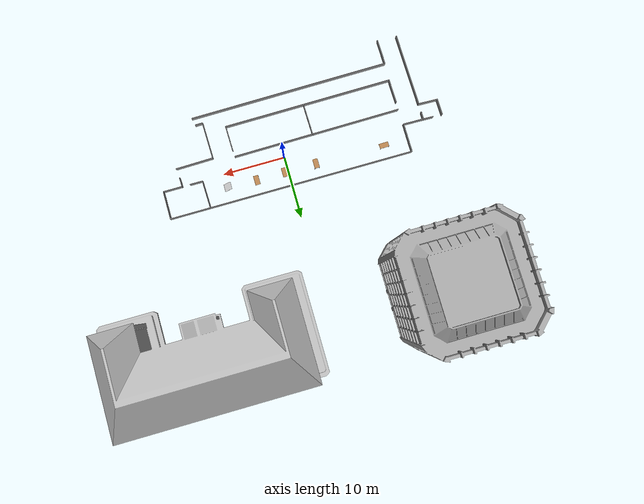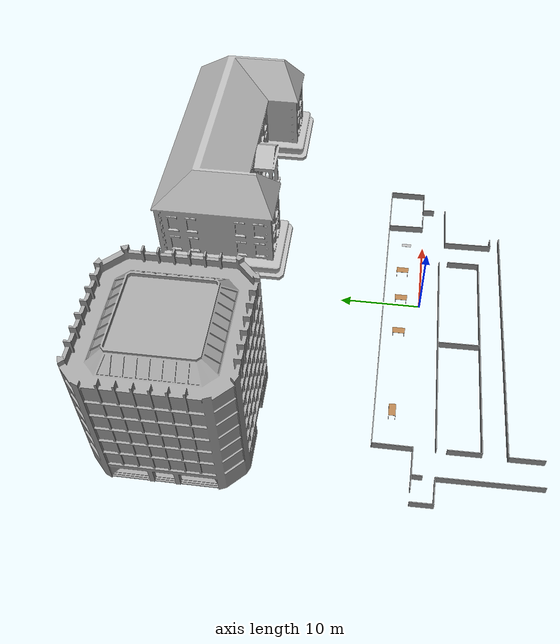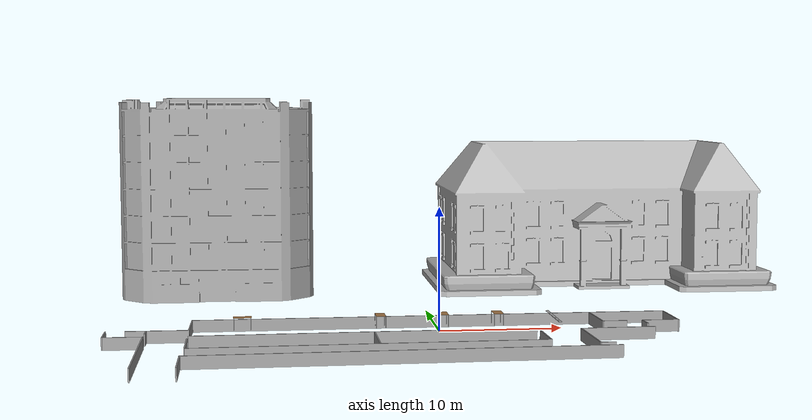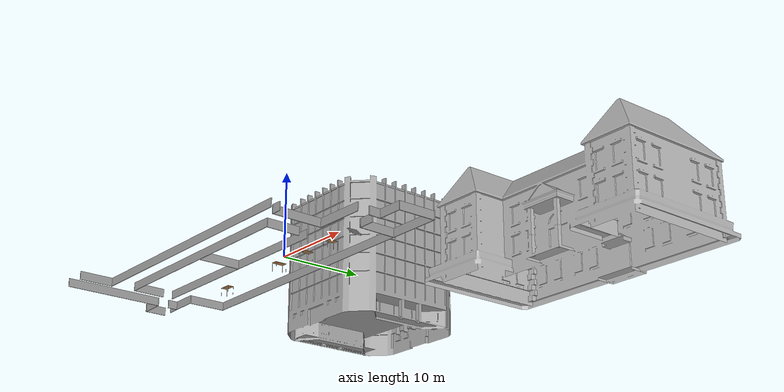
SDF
<?xml version='1.0'?>
<sdf version='1.6'>
  <model name='big_project_room'>
    <link name='link'>
      <pose frame=''>14.0349 -2.99213 2.5e-05 0 -0 0.019261</pose>
      <inertial>
        <mass>0.0501598</mass>
        <inertia>
          <ixx>0.00418042</ixx>
          <ixy>0</ixy>
          <ixz>0</ixz>
          <iyy>0.104263</iyy>
          <iyz>0</iyz>
          <izz>0.100083</izz>
        </inertia>
        <pose frame=''>0 0 0 0 -0 0</pose>
      </inertial>
      <self_collide>0</self_collide>
      <kinematic>0</kinematic>
      <visual name='visual'>
        <geometry>
          <box>
            <size>6.096 0.10251 1</size>
          </box>
        </geometry>
        <material>
          <script>
            <name>Gazebo/Grey</name>
            <uri>file://media/materials/scripts/gazebo.material</uri>
          </script>
          <shader type='pixel'>
            <normal_map>__default__</normal_map>
          </shader>
          <ambient>1 1 1 1</ambient>
          <diffuse>0.7 0.7 0.7 1</diffuse>
          <specular>0.01 0.01 0.01 1</specular>
          <emissive>0 0 0 1</emissive>
        </material>
        <pose frame=''>0 0 0 0 -0 0</pose>
        <transparency>0</transparency>
        <cast_shadows>1</cast_shadows>
      </visual>
      <collision name='collision'>
        <laser_retro>0</laser_retro>
        <max_contacts>10</max_contacts>
        <pose frame=''>0 0 0 0 -0 0</pose>
        <geometry>
          <box>
            <size>6.096 0.10251 1</size>
          </box>
        </geometry>
        <surface>
          <friction>
            <ode>
              <mu>1</mu>
              <mu2>1</mu2>
              <fdir1>0 0 0</fdir1>
              <slip1>0</slip1>
              <slip2>0</slip2>
            </ode>
            <torsional>
              <coefficient>1</coefficient>
              <patch_radius>0</patch_radius>
              <surface_radius>0</surface_radius>
              <use_patch_radius>1</use_patch_radius>
              <ode>
                <slip>0</slip>
              </ode>
            </torsional>
          </friction>
          <bounce>
            <restitution_coefficient>0</restitution_coefficient>
            <threshold>1e+06</threshold>
          </bounce>
          <contact>
            <collide_without_contact>0</collide_without_contact>
            <collide_without_contact_bitmask>1</collide_without_contact_bitmask>
            <collide_bitmask>1</collide_bitmask>
            <ode>
              <soft_cfm>0</soft_cfm>
              <soft_erp>0.2</soft_erp>
              <kp>1e+13</kp>
              <kd>1</kd>
              <max_vel>0.01</max_vel>
              <min_depth>0</min_depth>
            </ode>
            <bullet>
              <split_impulse>1</split_impulse>
              <split_impulse_penetration_threshold>-0.01</split_impulse_penetration_threshold>
              <soft_cfm>0</soft_cfm>
              <soft_erp>0.2</soft_erp>
              <kp>1e+13</kp>
              <kd>1</kd>
            </bullet>
          </contact>
        </surface>
      </collision>
    </link>
    <link name='link_0_clone'>
      <pose frame=''>19.9441 2.29599 -0.01875 0.00066 0.00066 -1.57077</pose>
      <inertial>
        <mass>1</mass>
        <inertia>
          <ixx>0.166667</ixx>
          <ixy>0</ixy>
          <ixz>0</ixz>
          <iyy>0.166667</iyy>
          <iyz>0</iyz>
          <izz>0.166667</izz>
        </inertia>
        <pose frame=''>0 0 0 0 -0 0</pose>
      </inertial>
      <self_collide>0</self_collide>
      <kinematic>0</kinematic>
      <gravity>1</gravity>
      <visual name='visual'>
        <pose frame=''>0 0 0 0 -0 0</pose>
        <geometry>
          <box>
            <size>4.527 0.1 1</size>
          </box>
        </geometry>
        <material>
          <lighting>1</lighting>
          <script>
            <uri>file://media/materials/scripts/gazebo.material</uri>
            <name>Gazebo/Grey</name>
          </script>
          <shader type='pixel'>
            <normal_map>__default__</normal_map>
          </shader>
          <ambient>1 1 1 1</ambient>
          <diffuse>0.7 0.7 0.7 1</diffuse>
          <specular>0.01 0.01 0.01 1</specular>
          <emissive>0 0 0 1</emissive>
        </material>
        <transparency>0</transparency>
        <cast_shadows>1</cast_shadows>
      </visual>
      <collision name='collision'>
        <laser_retro>0</laser_retro>
        <max_contacts>10</max_contacts>
        <pose frame=''>0 0 0 0 -0 0</pose>
        <geometry>
          <box>
            <size>4.572 0.1 1</size>
          </box>
        </geometry>
        <surface>
          <friction>
            <ode>
              <mu>1</mu>
              <mu2>1</mu2>
              <fdir1>0 0 0</fdir1>
              <slip1>0</slip1>
              <slip2>0</slip2>
            </ode>
            <torsional>
              <coefficient>1</coefficient>
              <patch_radius>0</patch_radius>
              <surface_radius>0</surface_radius>
              <use_patch_radius>1</use_patch_radius>
              <ode>
                <slip>0</slip>
              </ode>
            </torsional>
          </friction>
          <bounce>
            <restitution_coefficient>0</restitution_coefficient>
            <threshold>1e+06</threshold>
          </bounce>
          <contact>
            <collide_without_contact>0</collide_without_contact>
            <collide_without_contact_bitmask>1</collide_without_contact_bitmask>
            <collide_bitmask>1</collide_bitmask>
            <ode>
              <soft_cfm>0</soft_cfm>
              <soft_erp>0.2</soft_erp>
              <kp>1e+13</kp>
              <kd>1</kd>
              <max_vel>0.01</max_vel>
              <min_depth>0</min_depth>
            </ode>
            <bullet>
              <split_impulse>1</split_impulse>
              <split_impulse_penetration_threshold>-0.01</split_impulse_penetration_threshold>
              <soft_cfm>0</soft_cfm>
              <soft_erp>0.2</soft_erp>
              <kp>1e+13</kp>
              <kd>1</kd>
            </bullet>
          </contact>
        </surface>
      </collision>
    </link>
    <link name='link_0_clone_clone'>
      <pose frame=''>-19.9604 2.29143 -0.013844 0.00066 0 -1.57081</pose>
      <inertial>
        <mass>1</mass>
        <inertia>
          <ixx>0.166667</ixx>
          <ixy>0</ixy>
          <ixz>0</ixz>
          <iyy>0.166667</iyy>
          <iyz>0</iyz>
          <izz>0.166667</izz>
        </inertia>
        <pose frame=''>0 0 0 0 -0 0</pose>
      </inertial>
      <self_collide>0</self_collide>
      <kinematic>0</kinematic>
      <visual name='visual'>
        <pose frame=''>0 0 0 0 -0 0</pose>
        <geometry>
          <box>
            <size>4.527 0.1 1</size>
          </box>
        </geometry>
        <material>
          <lighting>1</lighting>
          <script>
            <uri>file://media/materials/scripts/gazebo.material</uri>
            <name>Gazebo/Grey</name>
          </script>
          <shader type='pixel'>
            <normal_map>__default__</normal_map>
          </shader>
          <ambient>1 1 1 1</ambient>
          <diffuse>0.7 0.7 0.7 1</diffuse>
          <specular>0.01 0.01 0.01 1</specular>
          <emissive>0 0 0 1</emissive>
        </material>
        <transparency>0</transparency>
        <cast_shadows>1</cast_shadows>
      </visual>
      <collision name='collision'>
        <laser_retro>0</laser_retro>
        <max_contacts>10</max_contacts>
        <pose frame=''>0 0 0 0 -0 0</pose>
        <geometry>
          <box>
            <size>4.572 0.1 1</size>
          </box>
        </geometry>
        <surface>
          <friction>
            <ode>
              <mu>1</mu>
              <mu2>1</mu2>
              <fdir1>0 0 0</fdir1>
              <slip1>0</slip1>
              <slip2>0</slip2>
            </ode>
            <torsional>
              <coefficient>1</coefficient>
              <patch_radius>0</patch_radius>
              <surface_radius>0</surface_radius>
              <use_patch_radius>1</use_patch_radius>
              <ode>
                <slip>0</slip>
              </ode>
            </torsional>
          </friction>
          <bounce>
            <restitution_coefficient>0</restitution_coefficient>
            <threshold>1e+06</threshold>
          </bounce>
          <contact>
            <collide_without_contact>0</collide_without_contact>
            <collide_without_contact_bitmask>1</collide_without_contact_bitmask>
            <collide_bitmask>1</collide_bitmask>
            <ode>
              <soft_cfm>0</soft_cfm>
              <soft_erp>0.2</soft_erp>
              <kp>1e+13</kp>
              <kd>1</kd>
              <max_vel>0.01</max_vel>
              <min_depth>0</min_depth>
            </ode>
            <bullet>
              <split_impulse>1</split_impulse>
              <split_impulse_penetration_threshold>-0.01</split_impulse_penetration_threshold>
              <soft_cfm>0</soft_cfm>
              <soft_erp>0.2</soft_erp>
              <kp>1e+13</kp>
              <kd>1</kd>
            </bullet>
          </contact>
        </surface>
      </collision>
    </link>
    <link name='link_0_clone_clone_clone_0'>
      <pose frame=''>14.5732 0.114647 0.004935 -0.000664 0.000656 3.13495</pose>
      <inertial>
        <mass>1</mass>
        <inertia>
          <ixx>0.166667</ixx>
          <ixy>0</ixy>
          <ixz>0</ixz>
          <iyy>0.166667</iyy>
          <iyz>0</iyz>
          <izz>0.166667</izz>
        </inertia>
        <pose frame=''>0 0 0 0 -0 0</pose>
      </inertial>
      <self_collide>0</self_collide>
      <kinematic>0</kinematic>
      <gravity>1</gravity>
      <visual name='visual'>
        <pose frame=''>0 0 0 0 -0 0</pose>
        <geometry>
          <box>
            <size>2 0.1 1</size>
          </box>
        </geometry>
        <material>
          <lighting>1</lighting>
          <script>
            <uri>file://media/materials/scripts/gazebo.material</uri>
            <name>Gazebo/Grey</name>
          </script>
          <shader type='pixel'>
            <normal_map>__default__</normal_map>
          </shader>
          <ambient>1 1 1 1</ambient>
          <diffuse>0.7 0.7 0.7 1</diffuse>
          <specular>0.01 0.01 0.01 1</specular>
          <emissive>0 0 0 1</emissive>
        </material>
        <transparency>0</transparency>
        <cast_shadows>1</cast_shadows>
      </visual>
      <collision name='collision'>
        <laser_retro>0</laser_retro>
        <max_contacts>10</max_contacts>
        <pose frame=''>0 0 0 0 -0 0</pose>
        <geometry>
          <box>
            <size>2 0.1 1</size>
          </box>
        </geometry>
        <surface>
          <friction>
            <ode>
              <mu>1</mu>
              <mu2>1</mu2>
              <fdir1>0 0 0</fdir1>
              <slip1>0</slip1>
              <slip2>0</slip2>
            </ode>
            <torsional>
              <coefficient>1</coefficient>
              <patch_radius>0</patch_radius>
              <surface_radius>0</surface_radius>
              <use_patch_radius>1</use_patch_radius>
              <ode>
                <slip>0</slip>
              </ode>
            </torsional>
          </friction>
          <bounce>
            <restitution_coefficient>0</restitution_coefficient>
            <threshold>1e+06</threshold>
          </bounce>
          <contact>
            <collide_without_contact>0</collide_without_contact>
            <collide_without_contact_bitmask>1</collide_without_contact_bitmask>
            <collide_bitmask>1</collide_bitmask>
            <ode>
              <soft_cfm>0</soft_cfm>
              <soft_erp>0.2</soft_erp>
              <kp>1e+13</kp>
              <kd>1</kd>
              <max_vel>0.01</max_vel>
              <min_depth>0</min_depth>
            </ode>
            <bullet>
              <split_impulse>1</split_impulse>
              <split_impulse_penetration_threshold>-0.01</split_impulse_penetration_threshold>
              <soft_cfm>0</soft_cfm>
              <soft_erp>0.2</soft_erp>
              <kp>1e+13</kp>
              <kd>1</kd>
            </bullet>
          </contact>
        </surface>
      </collision>
    </link>
    <link name='link_0_clone_clone_clone_clone_0'>
      <pose frame=''>16.8828 -0.632141 0.009219 -0.000709 -0.001294 1.60824</pose>
      <inertial>
        <mass>1</mass>
        <inertia>
          <ixx>0.166667</ixx>
          <ixy>0</ixy>
          <ixz>0</ixz>
          <iyy>0.166667</iyy>
          <iyz>0</iyz>
          <izz>0.166667</izz>
        </inertia>
        <pose frame=''>0 0 0 0 -0 0</pose>
      </inertial>
      <self_collide>0</self_collide>
      <kinematic>0</kinematic>
      <visual name='visual'>
        <pose frame=''>0 0 0 0 -0 0</pose>
        <geometry>
          <box>
            <size>1.524 0.1 1</size>
          </box>
        </geometry>
        <material>
          <lighting>1</lighting>
          <script>
            <uri>file://media/materials/scripts/gazebo.material</uri>
            <name>Gazebo/Grey</name>
          </script>
          <shader type='pixel'>
            <normal_map>__default__</normal_map>
          </shader>
          <ambient>1 1 1 1</ambient>
          <diffuse>0.7 0.7 0.7 1</diffuse>
          <specular>0.01 0.01 0.01 1</specular>
          <emissive>0 0 0 1</emissive>
        </material>
        <transparency>0</transparency>
        <cast_shadows>1</cast_shadows>
      </visual>
      <collision name='collision'>
        <laser_retro>0</laser_retro>
        <max_contacts>10</max_contacts>
        <pose frame=''>0 0 0 0 -0 0</pose>
        <geometry>
          <box>
            <size>1.524 0.1 1</size>
          </box>
        </geometry>
        <surface>
          <friction>
            <ode>
              <mu>1</mu>
              <mu2>1</mu2>
              <fdir1>0 0 0</fdir1>
              <slip1>0</slip1>
              <slip2>0</slip2>
            </ode>
            <torsional>
              <coefficient>1</coefficient>
              <patch_radius>0</patch_radius>
              <surface_radius>0</surface_radius>
              <use_patch_radius>1</use_patch_radius>
              <ode>
                <slip>0</slip>
              </ode>
            </torsional>
          </friction>
          <bounce>
            <restitution_coefficient>0</restitution_coefficient>
            <threshold>1e+06</threshold>
          </bounce>
          <contact>
            <collide_without_contact>0</collide_without_contact>
            <collide_without_contact_bitmask>1</collide_without_contact_bitmask>
            <collide_bitmask>1</collide_bitmask>
            <ode>
              <soft_cfm>0</soft_cfm>
              <soft_erp>0.2</soft_erp>
              <kp>1e+13</kp>
              <kd>1</kd>
              <max_vel>0.01</max_vel>
              <min_depth>0</min_depth>
            </ode>
            <bullet>
              <split_impulse>1</split_impulse>
              <split_impulse_penetration_threshold>-0.01</split_impulse_penetration_threshold>
              <soft_cfm>0</soft_cfm>
              <soft_erp>0.2</soft_erp>
              <kp>1e+13</kp>
              <kd>1</kd>
            </bullet>
          </contact>
        </surface>
      </collision>
    </link>
    <link name='link_0_clone_clone_clone_clone_1'>
      <pose frame=''>18.3965 0.082315 0.010039 -0.001319 0.000662 -3.14011</pose>
      <inertial>
        <mass>1</mass>
        <inertia>
          <ixx>0.166667</ixx>
          <ixy>0</ixy>
          <ixz>0</ixz>
          <iyy>0.166667</iyy>
          <iyz>0</iyz>
          <izz>0.166667</izz>
        </inertia>
        <pose frame=''>0 0 0 0 -0 0</pose>
      </inertial>
      <self_collide>0</self_collide>
      <kinematic>0</kinematic>
      <gravity>1</gravity>
      <visual name='visual'>
        <pose frame=''>0 0 0 0 -0 0</pose>
        <geometry>
          <box>
            <size>3 0.1 1</size>
          </box>
        </geometry>
        <material>
          <lighting>1</lighting>
          <script>
            <uri>file://media/materials/scripts/gazebo.material</uri>
            <name>Gazebo/Grey</name>
          </script>
          <shader type='pixel'>
            <normal_map>__default__</normal_map>
          </shader>
          <ambient>1 1 1 1</ambient>
          <diffuse>0.7 0.7 0.7 1</diffuse>
          <specular>0.01 0.01 0.01 1</specular>
          <emissive>0 0 0 1</emissive>
        </material>
        <transparency>0</transparency>
        <cast_shadows>1</cast_shadows>
      </visual>
      <collision name='collision'>
        <laser_retro>0</laser_retro>
        <max_contacts>10</max_contacts>
        <pose frame=''>0 0 0 0 -0 0</pose>
        <geometry>
          <box>
            <size>3 0.1 1</size>
          </box>
        </geometry>
        <surface>
          <friction>
            <ode>
              <mu>1</mu>
              <mu2>1</mu2>
              <fdir1>0 0 0</fdir1>
              <slip1>0</slip1>
              <slip2>0</slip2>
            </ode>
            <torsional>
              <coefficient>1</coefficient>
              <patch_radius>0</patch_radius>
              <surface_radius>0</surface_radius>
              <use_patch_radius>1</use_patch_radius>
              <ode>
                <slip>0</slip>
              </ode>
            </torsional>
          </friction>
          <bounce>
            <restitution_coefficient>0</restitution_coefficient>
            <threshold>1e+06</threshold>
          </bounce>
          <contact>
            <collide_without_contact>0</collide_without_contact>
            <collide_without_contact_bitmask>1</collide_without_contact_bitmask>
            <collide_bitmask>1</collide_bitmask>
            <ode>
              <soft_cfm>0</soft_cfm>
              <soft_erp>0.2</soft_erp>
              <kp>1e+13</kp>
              <kd>1</kd>
              <max_vel>0.01</max_vel>
              <min_depth>0</min_depth>
            </ode>
            <bullet>
              <split_impulse>1</split_impulse>
              <split_impulse_penetration_threshold>-0.01</split_impulse_penetration_threshold>
              <soft_cfm>0</soft_cfm>
              <soft_erp>0.2</soft_erp>
              <kp>1e+13</kp>
              <kd>1</kd>
            </bullet>
          </contact>
        </surface>
      </collision>
    </link>
    <link name='link_clone'>
      <pose frame=''>-0.007377 4.60801 0.003041 0.00066 -0 0</pose>
      <inertial>
        <mass>0.0501598</mass>
        <inertia>
          <ixx>0.00418042</ixx>
          <ixy>0</ixy>
          <ixz>0</ixz>
          <iyy>0.104263</iyy>
          <iyz>0</iyz>
          <izz>0.100083</izz>
        </inertia>
        <pose frame=''>0 0 0 0 -0 0</pose>
      </inertial>
      <self_collide>0</self_collide>
      <kinematic>0</kinematic>
      <gravity>1</gravity>
      <visual name='visual'>
        <geometry>
          <box>
            <size>40 0.10251 1</size>
          </box>
        </geometry>
        <material>
          <script>
            <name>Gazebo/Grey</name>
            <uri>file://media/materials/scripts/gazebo.material</uri>
          </script>
          <shader type='pixel'>
            <normal_map>__default__</normal_map>
          </shader>
          <ambient>1 1 1 1</ambient>
          <diffuse>0.7 0.7 0.7 1</diffuse>
          <specular>0.01 0.01 0.01 1</specular>
          <emissive>0 0 0 1</emissive>
        </material>
        <pose frame=''>0 0 0 0 -0 0</pose>
        <transparency>0</transparency>
        <cast_shadows>1</cast_shadows>
      </visual>
      <collision name='collision'>
        <laser_retro>0</laser_retro>
        <max_contacts>10</max_contacts>
        <pose frame=''>0 0 0 0 -0 0</pose>
        <geometry>
          <box>
            <size>40 0.10251 1</size>
          </box>
        </geometry>
        <surface>
          <friction>
            <ode>
              <mu>1</mu>
              <mu2>1</mu2>
              <fdir1>0 0 0</fdir1>
              <slip1>0</slip1>
              <slip2>0</slip2>
            </ode>
            <torsional>
              <coefficient>1</coefficient>
              <patch_radius>0</patch_radius>
              <surface_radius>0</surface_radius>
              <use_patch_radius>1</use_patch_radius>
              <ode>
                <slip>0</slip>
              </ode>
            </torsional>
          </friction>
          <bounce>
            <restitution_coefficient>0</restitution_coefficient>
            <threshold>1e+06</threshold>
          </bounce>
          <contact>
            <collide_without_contact>0</collide_without_contact>
            <collide_without_contact_bitmask>1</collide_without_contact_bitmask>
            <collide_bitmask>1</collide_bitmask>
            <ode>
              <soft_cfm>0</soft_cfm>
              <soft_erp>0.2</soft_erp>
              <kp>1e+13</kp>
              <kd>1</kd>
              <max_vel>0.01</max_vel>
              <min_depth>0</min_depth>
            </ode>
            <bullet>
              <split_impulse>1</split_impulse>
              <split_impulse_penetration_threshold>-0.01</split_impulse_penetration_threshold>
              <soft_cfm>0</soft_cfm>
              <soft_erp>0.2</soft_erp>
              <kp>1e+13</kp>
              <kd>1</kd>
            </bullet>
          </contact>
        </surface>
      </collision>
    </link>
    <link name='link_clone_0'>
      <pose frame=''>13.4826 2.33415 0.001565 1.7e-05 0.00066 -1.54442</pose>
      <inertial>
        <mass>0.0373227</mass>
        <inertia>
          <ixx>0.00314291</ixx>
          <ixy>0</ixy>
          <ixz>0</ixz>
          <iyy>0.067101</iyy>
          <iyz>0</iyz>
          <izz>0.0640235</izz>
        </inertia>
        <pose frame=''>0 0 0 0 -0 0</pose>
      </inertial>
      <self_collide>0</self_collide>
      <kinematic>0</kinematic>
      <gravity>1</gravity>
      <visual name='visual'>
        <geometry>
          <box>
            <size>4.53589 0.10251 1</size>
          </box>
        </geometry>
        <material>
          <script>
            <name>Gazebo/Grey</name>
            <uri>file://media/materials/scripts/gazebo.material</uri>
          </script>
          <shader type='pixel'>
            <normal_map>__default__</normal_map>
          </shader>
          <ambient>1 1 1 1</ambient>
          <diffuse>0.7 0.7 0.7 1</diffuse>
          <specular>0.01 0.01 0.01 1</specular>
          <emissive>0 0 0 1</emissive>
        </material>
        <pose frame=''>0 0 0 0 -0 0</pose>
        <transparency>0</transparency>
        <cast_shadows>1</cast_shadows>
      </visual>
      <collision name='collision'>
        <laser_retro>0</laser_retro>
        <max_contacts>10</max_contacts>
        <pose frame=''>0 0 0 0 -0 0</pose>
        <geometry>
          <box>
            <size>4.53589 0.10251 1</size>
          </box>
        </geometry>
        <surface>
          <friction>
            <ode>
              <mu>1</mu>
              <mu2>1</mu2>
              <fdir1>0 0 0</fdir1>
              <slip1>0</slip1>
              <slip2>0</slip2>
            </ode>
            <torsional>
              <coefficient>1</coefficient>
              <patch_radius>0</patch_radius>
              <surface_radius>0</surface_radius>
              <use_patch_radius>1</use_patch_radius>
              <ode>
                <slip>0</slip>
              </ode>
            </torsional>
          </friction>
          <bounce>
            <restitution_coefficient>0</restitution_coefficient>
            <threshold>1e+06</threshold>
          </bounce>
          <contact>
            <collide_without_contact>0</collide_without_contact>
            <collide_without_contact_bitmask>1</collide_without_contact_bitmask>
            <collide_bitmask>1</collide_bitmask>
            <ode>
              <soft_cfm>0</soft_cfm>
              <soft_erp>0.2</soft_erp>
              <kp>1e+13</kp>
              <kd>1</kd>
              <max_vel>0.01</max_vel>
              <min_depth>0</min_depth>
            </ode>
            <bullet>
              <split_impulse>1</split_impulse>
              <split_impulse_penetration_threshold>-0.01</split_impulse_penetration_threshold>
              <soft_cfm>0</soft_cfm>
              <soft_erp>0.2</soft_erp>
              <kp>1e+13</kp>
              <kd>1</kd>
            </bullet>
          </contact>
        </surface>
      </collision>
    </link>
    <link name='link_clone_1'>
      <pose frame=''>11.064 -6.05479 -0.003971 1.2e-05 0.00066 -1.55284</pose>
      <inertial>
        <mass>0.0501598</mass>
        <inertia>
          <ixx>0.00418042</ixx>
          <ixy>0</ixy>
          <ixz>0</ixz>
          <iyy>0.104263</iyy>
          <iyz>0</iyz>
          <izz>0.100083</izz>
        </inertia>
        <pose frame=''>0 0 0 0 -0 0</pose>
      </inertial>
      <self_collide>0</self_collide>
      <kinematic>0</kinematic>
      <visual name='visual'>
        <geometry>
          <box>
            <size>6.096 0.10251 1</size>
          </box>
        </geometry>
        <material>
          <script>
            <name>Gazebo/Grey</name>
            <uri>file://media/materials/scripts/gazebo.material</uri>
          </script>
          <shader type='pixel'>
            <normal_map>__default__</normal_map>
          </shader>
          <ambient>1 1 1 1</ambient>
          <diffuse>0.7 0.7 0.7 1</diffuse>
          <specular>0.01 0.01 0.01 1</specular>
          <emissive>0 0 0 1</emissive>
        </material>
        <pose frame=''>0 0 0 0 -0 0</pose>
        <transparency>0</transparency>
        <cast_shadows>1</cast_shadows>
      </visual>
      <collision name='collision'>
        <laser_retro>0</laser_retro>
        <max_contacts>10</max_contacts>
        <pose frame=''>0 0 0 0 -0 0</pose>
        <geometry>
          <box>
            <size>6.096 0.10251 1</size>
          </box>
        </geometry>
        <surface>
          <friction>
            <ode>
              <mu>1</mu>
              <mu2>1</mu2>
              <fdir1>0 0 0</fdir1>
              <slip1>0</slip1>
              <slip2>0</slip2>
            </ode>
            <torsional>
              <coefficient>1</coefficient>
              <patch_radius>0</patch_radius>
              <surface_radius>0</surface_radius>
              <use_patch_radius>1</use_patch_radius>
              <ode>
                <slip>0</slip>
              </ode>
            </torsional>
          </friction>
          <bounce>
            <restitution_coefficient>0</restitution_coefficient>
            <threshold>1e+06</threshold>
          </bounce>
          <contact>
            <collide_without_contact>0</collide_without_contact>
            <collide_without_contact_bitmask>1</collide_without_contact_bitmask>
            <collide_bitmask>1</collide_bitmask>
            <ode>
              <soft_cfm>0</soft_cfm>
              <soft_erp>0.2</soft_erp>
              <kp>1e+13</kp>
              <kd>1</kd>
              <max_vel>0.01</max_vel>
              <min_depth>0</min_depth>
            </ode>
            <bullet>
              <split_impulse>1</split_impulse>
              <split_impulse_penetration_threshold>-0.01</split_impulse_penetration_threshold>
              <soft_cfm>0</soft_cfm>
              <soft_erp>0.2</soft_erp>
              <kp>1e+13</kp>
              <kd>1</kd>
            </bullet>
          </contact>
        </surface>
      </collision>
    </link>
    <link name='link_clone_1_clone'>
      <pose frame=''>-3.72157 -10.3844 -0.010858 -0.00132 1.3e-05 -3.13177</pose>
      <inertial>
        <mass>0.268169</mass>
        <inertia>
          <ixx>0.0225823</ixx>
          <ixy>0</ixy>
          <ixz>0</ixz>
          <iyy>23.7593</iyy>
          <iyz>0</iyz>
          <izz>23.7372</izz>
        </inertia>
        <pose frame=''>0 0 0 0 -0 0</pose>
      </inertial>
      <self_collide>0</self_collide>
      <kinematic>0</kinematic>
      <visual name='visual'>
        <geometry>
          <box>
            <size>32.5911 0.10251 1</size>
          </box>
        </geometry>
        <material>
          <script>
            <name>Gazebo/Grey</name>
            <uri>file://media/materials/scripts/gazebo.material</uri>
          </script>
          <shader type='pixel'>
            <normal_map>__default__</normal_map>
          </shader>
          <ambient>1 1 1 1</ambient>
          <diffuse>0.7 0.7 0.7 1</diffuse>
          <specular>0.01 0.01 0.01 1</specular>
          <emissive>0 0 0 1</emissive>
        </material>
        <pose frame=''>0 0 0 0 -0 0</pose>
        <transparency>0</transparency>
        <cast_shadows>1</cast_shadows>
      </visual>
      <collision name='collision'>
        <laser_retro>0</laser_retro>
        <max_contacts>10</max_contacts>
        <pose frame=''>0 0 0 0 -0 0</pose>
        <geometry>
          <box>
            <size>32.5911 0.10251 1</size>
          </box>
        </geometry>
        <surface>
          <friction>
            <ode>
              <mu>1</mu>
              <mu2>1</mu2>
              <fdir1>0 0 0</fdir1>
              <slip1>0</slip1>
              <slip2>0</slip2>
            </ode>
            <torsional>
              <coefficient>1</coefficient>
              <patch_radius>0</patch_radius>
              <surface_radius>0</surface_radius>
              <use_patch_radius>1</use_patch_radius>
              <ode>
                <slip>0</slip>
              </ode>
            </torsional>
          </friction>
          <bounce>
            <restitution_coefficient>0</restitution_coefficient>
            <threshold>1e+06</threshold>
          </bounce>
          <contact>
            <collide_without_contact>0</collide_without_contact>
            <collide_without_contact_bitmask>1</collide_without_contact_bitmask>
            <collide_bitmask>1</collide_bitmask>
            <ode>
              <soft_cfm>0</soft_cfm>
              <soft_erp>0.2</soft_erp>
              <kp>1e+13</kp>
              <kd>1</kd>
              <max_vel>0.01</max_vel>
              <min_depth>0</min_depth>
            </ode>
            <bullet>
              <split_impulse>1</split_impulse>
              <split_impulse_penetration_threshold>-0.01</split_impulse_penetration_threshold>
              <soft_cfm>0</soft_cfm>
              <soft_erp>0.2</soft_erp>
              <kp>1e+13</kp>
              <kd>1</kd>
            </bullet>
          </contact>
        </surface>
      </collision>
    </link>
    <link name='link_clone_1_clone_0'>
      <pose frame=''>11.726 -9.03721 -0.009925 -0.00132 2.9e-05 -3.11953</pose>
      <inertial>
        <mass>0.00975708</mass>
        <inertia>
          <ixx>0.000821634</ixx>
          <ixy>0</ixy>
          <ixz>0</ixz>
          <iyy>0.00195639</iyy>
          <iyz>0</iyz>
          <izz>0.00115184</izz>
        </inertia>
        <pose frame=''>0 0 0 0 -0 0</pose>
      </inertial>
      <self_collide>0</self_collide>
      <kinematic>0</kinematic>
      <visual name='visual'>
        <geometry>
          <box>
            <size>1.1858 0.10251 1</size>
          </box>
        </geometry>
        <material>
          <script>
            <name>Gazebo/Grey</name>
            <uri>file://media/materials/scripts/gazebo.material</uri>
          </script>
          <shader type='pixel'>
            <normal_map>__default__</normal_map>
          </shader>
          <ambient>1 1 1 1</ambient>
          <diffuse>0.7 0.7 0.7 1</diffuse>
          <specular>0.01 0.01 0.01 1</specular>
          <emissive>0 0 0 1</emissive>
        </material>
        <pose frame=''>0 0 0 0 -0 0</pose>
        <transparency>0</transparency>
        <cast_shadows>1</cast_shadows>
      </visual>
      <collision name='collision'>
        <laser_retro>0</laser_retro>
        <max_contacts>10</max_contacts>
        <pose frame=''>0 0 0 0 -0 0</pose>
        <geometry>
          <box>
            <size>1.1858 0.10251 1</size>
          </box>
        </geometry>
        <surface>
          <friction>
            <ode>
              <mu>1</mu>
              <mu2>1</mu2>
              <fdir1>0 0 0</fdir1>
              <slip1>0</slip1>
              <slip2>0</slip2>
            </ode>
            <torsional>
              <coefficient>1</coefficient>
              <patch_radius>0</patch_radius>
              <surface_radius>0</surface_radius>
              <use_patch_radius>1</use_patch_radius>
              <ode>
                <slip>0</slip>
              </ode>
            </torsional>
          </friction>
          <bounce>
            <restitution_coefficient>0</restitution_coefficient>
            <threshold>1e+06</threshold>
          </bounce>
          <contact>
            <collide_without_contact>0</collide_without_contact>
            <collide_without_contact_bitmask>1</collide_without_contact_bitmask>
            <collide_bitmask>1</collide_bitmask>
            <ode>
              <soft_cfm>0</soft_cfm>
              <soft_erp>0.2</soft_erp>
              <kp>1e+13</kp>
              <kd>1</kd>
              <max_vel>0.01</max_vel>
              <min_depth>0</min_depth>
            </ode>
            <bullet>
              <split_impulse>1</split_impulse>
              <split_impulse_penetration_threshold>-0.01</split_impulse_penetration_threshold>
              <soft_cfm>0</soft_cfm>
              <soft_erp>0.2</soft_erp>
              <kp>1e+13</kp>
              <kd>1</kd>
            </bullet>
          </contact>
        </surface>
      </collision>
    </link>
    <link name='link_clone_1_clone_1'>
      <pose frame=''>-21.5976 0.008554 -0.003949 0.00132 2.1e-05 -0.016034</pose>
      <inertial>
        <mass>0.0277737</mass>
        <inertia>
          <ixx>0.0023388</ixx>
          <ixy>0</ixy>
          <ixz>0</ixz>
          <iyy>0.0286838</iyy>
          <iyz>0</iyz>
          <izz>0.0263937</izz>
        </inertia>
        <pose frame=''>0 0 0 0 -0 0</pose>
      </inertial>
      <self_collide>0</self_collide>
      <kinematic>0</kinematic>
      <visual name='visual'>
        <geometry>
          <box>
            <size>3.37539 0.10251 1</size>
          </box>
        </geometry>
        <material>
          <script>
            <name>Gazebo/Grey</name>
            <uri>file://media/materials/scripts/gazebo.material</uri>
          </script>
          <shader type='pixel'>
            <normal_map>__default__</normal_map>
          </shader>
          <ambient>1 1 1 1</ambient>
          <diffuse>0.7 0.7 0.7 1</diffuse>
          <specular>0.01 0.01 0.01 1</specular>
          <emissive>0 0 0 1</emissive>
        </material>
        <pose frame=''>0 0 0 0 -0 0</pose>
        <transparency>0</transparency>
        <cast_shadows>1</cast_shadows>
      </visual>
      <collision name='collision'>
        <laser_retro>0</laser_retro>
        <max_contacts>10</max_contacts>
        <pose frame=''>0 0 0 0 -0 0</pose>
        <geometry>
          <box>
            <size>3.37539 0.10251 1</size>
          </box>
        </geometry>
        <surface>
          <friction>
            <ode>
              <mu>1</mu>
              <mu2>1</mu2>
              <fdir1>0 0 0</fdir1>
              <slip1>0</slip1>
              <slip2>0</slip2>
            </ode>
            <torsional>
              <coefficient>1</coefficient>
              <patch_radius>0</patch_radius>
              <surface_radius>0</surface_radius>
              <use_patch_radius>1</use_patch_radius>
              <ode>
                <slip>0</slip>
              </ode>
            </torsional>
          </friction>
          <bounce>
            <restitution_coefficient>0</restitution_coefficient>
            <threshold>1e+06</threshold>
          </bounce>
          <contact>
            <collide_without_contact>0</collide_without_contact>
            <collide_without_contact_bitmask>1</collide_without_contact_bitmask>
            <collide_bitmask>1</collide_bitmask>
            <ode>
              <soft_cfm>0</soft_cfm>
              <soft_erp>0.2</soft_erp>
              <kp>1e+13</kp>
              <kd>1</kd>
              <max_vel>0.01</max_vel>
              <min_depth>0</min_depth>
            </ode>
            <bullet>
              <split_impulse>1</split_impulse>
              <split_impulse_penetration_threshold>-0.01</split_impulse_penetration_threshold>
              <soft_cfm>0</soft_cfm>
              <soft_erp>0.2</soft_erp>
              <kp>1e+13</kp>
              <kd>1</kd>
            </bullet>
          </contact>
        </surface>
      </collision>
    </link>
    <link name='link_clone_1_clone_2'>
      <pose frame=''>-26.3913 -1.18616 -0.004231 2e-05 0.00132 -1.55514</pose>
      <inertial>
        <mass>0.0221356</mass>
        <inertia>
          <ixx>0.00186402</ixx>
          <ixy>0</ixy>
          <ixz>0</ixz>
          <iyy>0.0151943</iyy>
          <iyz>0</iyz>
          <izz>0.0133691</izz>
        </inertia>
        <pose frame=''>0 0 0 0 -0 0</pose>
      </inertial>
      <self_collide>0</self_collide>
      <kinematic>0</kinematic>
      <visual name='visual'>
        <geometry>
          <box>
            <size>2.69018 0.10251 1</size>
          </box>
        </geometry>
        <material>
          <script>
            <name>Gazebo/Grey</name>
            <uri>file://media/materials/scripts/gazebo.material</uri>
          </script>
          <shader type='pixel'>
            <normal_map>__default__</normal_map>
          </shader>
          <ambient>1 1 1 1</ambient>
          <diffuse>0.7 0.7 0.7 1</diffuse>
          <specular>0.01 0.01 0.01 1</specular>
          <emissive>0 0 0 1</emissive>
        </material>
        <pose frame=''>0 0 0 0 -0 0</pose>
        <transparency>0</transparency>
        <cast_shadows>1</cast_shadows>
      </visual>
      <collision name='collision'>
        <laser_retro>0</laser_retro>
        <max_contacts>10</max_contacts>
        <pose frame=''>0 0 0 0 -0 0</pose>
        <geometry>
          <box>
            <size>2.69018 0.10251 1</size>
          </box>
        </geometry>
        <surface>
          <friction>
            <ode>
              <mu>1</mu>
              <mu2>1</mu2>
              <fdir1>0 0 0</fdir1>
              <slip1>0</slip1>
              <slip2>0</slip2>
            </ode>
            <torsional>
              <coefficient>1</coefficient>
              <patch_radius>0</patch_radius>
              <surface_radius>0</surface_radius>
              <use_patch_radius>1</use_patch_radius>
              <ode>
                <slip>0</slip>
              </ode>
            </torsional>
          </friction>
          <bounce>
            <restitution_coefficient>0</restitution_coefficient>
            <threshold>1e+06</threshold>
          </bounce>
          <contact>
            <collide_without_contact>0</collide_without_contact>
            <collide_without_contact_bitmask>1</collide_without_contact_bitmask>
            <collide_bitmask>1</collide_bitmask>
            <ode>
              <soft_cfm>0</soft_cfm>
              <soft_erp>0.2</soft_erp>
              <kp>1e+13</kp>
              <kd>1</kd>
              <max_vel>0.01</max_vel>
              <min_depth>0</min_depth>
            </ode>
            <bullet>
              <split_impulse>1</split_impulse>
              <split_impulse_penetration_threshold>-0.01</split_impulse_penetration_threshold>
              <soft_cfm>0</soft_cfm>
              <soft_erp>0.2</soft_erp>
              <kp>1e+13</kp>
              <kd>1</kd>
            </bullet>
          </contact>
        </surface>
      </collision>
    </link>
    <link name='link_clone_1_clone_2_clone'>
      <pose frame=''>-24.7939 -2.51572 -0.005884 -0.001979 -6.5e-05 3.10906</pose>
      <inertial>
        <mass>0.0257709</mass>
        <inertia>
          <ixx>0.00217014</ixx>
          <ixy>0</ixy>
          <ixz>0</ixz>
          <iyy>0.0232138</iyy>
          <iyz>0</iyz>
          <izz>0.0210888</izz>
        </inertia>
        <pose frame=''>0 0 0 0 -0 0</pose>
      </inertial>
      <self_collide>0</self_collide>
      <kinematic>0</kinematic>
      <visual name='visual'>
        <geometry>
          <box>
            <size>3.13198 0.10251 1</size>
          </box>
        </geometry>
        <material>
          <script>
            <name>Gazebo/Grey</name>
            <uri>file://media/materials/scripts/gazebo.material</uri>
          </script>
          <shader type='pixel'>
            <normal_map>__default__</normal_map>
          </shader>
          <ambient>1 1 1 1</ambient>
          <diffuse>0.7 0.7 0.7 1</diffuse>
          <specular>0.01 0.01 0.01 1</specular>
          <emissive>0 0 0 1</emissive>
        </material>
        <pose frame=''>0 0 0 0 -0 0</pose>
        <transparency>0</transparency>
        <cast_shadows>1</cast_shadows>
      </visual>
      <collision name='collision'>
        <laser_retro>0</laser_retro>
        <max_contacts>10</max_contacts>
        <pose frame=''>0 0 0 0 -0 0</pose>
        <geometry>
          <box>
            <size>3.13198 0.10251 1</size>
          </box>
        </geometry>
        <surface>
          <friction>
            <ode>
              <mu>1</mu>
              <mu2>1</mu2>
              <fdir1>0 0 0</fdir1>
              <slip1>0</slip1>
              <slip2>0</slip2>
            </ode>
            <torsional>
              <coefficient>1</coefficient>
              <patch_radius>0</patch_radius>
              <surface_radius>0</surface_radius>
              <use_patch_radius>1</use_patch_radius>
              <ode>
                <slip>0</slip>
              </ode>
            </torsional>
          </friction>
          <bounce>
            <restitution_coefficient>0</restitution_coefficient>
            <threshold>1e+06</threshold>
          </bounce>
          <contact>
            <collide_without_contact>0</collide_without_contact>
            <collide_without_contact_bitmask>1</collide_without_contact_bitmask>
            <collide_bitmask>1</collide_bitmask>
            <ode>
              <soft_cfm>0</soft_cfm>
              <soft_erp>0.2</soft_erp>
              <kp>1e+13</kp>
              <kd>1</kd>
              <max_vel>0.01</max_vel>
              <min_depth>0</min_depth>
            </ode>
            <bullet>
              <split_impulse>1</split_impulse>
              <split_impulse_penetration_threshold>-0.01</split_impulse_penetration_threshold>
              <soft_cfm>0</soft_cfm>
              <soft_erp>0.2</soft_erp>
              <kp>1e+13</kp>
              <kd>1</kd>
            </bullet>
          </contact>
        </surface>
      </collision>
    </link>
    <link name='link_clone_1_clone_2_clone_0'>
      <pose frame=''>-23.1913 -8.51767 -0.015724 3e-05 0.00198 -1.55514</pose>
      <inertial>
        <mass>0.0981255</mass>
        <inertia>
          <ixx>0.00826305</ixx>
          <ixy>0</ixy>
          <ixz>0</ixz>
          <iyy>1.17108</iyy>
          <iyz>0</iyz>
          <izz>1.16299</izz>
        </inertia>
        <pose frame=''>0 0 0 0 -0 0</pose>
      </inertial>
      <self_collide>0</self_collide>
      <kinematic>0</kinematic>
      <visual name='visual'>
        <geometry>
          <box>
            <size>11.9254 0.10251 1</size>
          </box>
        </geometry>
        <material>
          <script>
            <name>Gazebo/Grey</name>
            <uri>file://media/materials/scripts/gazebo.material</uri>
          </script>
          <shader type='pixel'>
            <normal_map>__default__</normal_map>
          </shader>
          <ambient>1 1 1 1</ambient>
          <diffuse>0.7 0.7 0.7 1</diffuse>
          <specular>0.01 0.01 0.01 1</specular>
          <emissive>0 0 0 1</emissive>
        </material>
        <pose frame=''>0 0 0 0 -0 0</pose>
        <transparency>0</transparency>
        <cast_shadows>1</cast_shadows>
      </visual>
      <collision name='collision'>
        <laser_retro>0</laser_retro>
        <max_contacts>10</max_contacts>
        <pose frame=''>0 0 0 0 -0 0</pose>
        <geometry>
          <box>
            <size>11.9254 0.10251 1</size>
          </box>
        </geometry>
        <surface>
          <friction>
            <ode>
              <mu>1</mu>
              <mu2>1</mu2>
              <fdir1>0 0 0</fdir1>
              <slip1>0</slip1>
              <slip2>0</slip2>
            </ode>
            <torsional>
              <coefficient>1</coefficient>
              <patch_radius>0</patch_radius>
              <surface_radius>0</surface_radius>
              <use_patch_radius>1</use_patch_radius>
              <ode>
                <slip>0</slip>
              </ode>
            </torsional>
          </friction>
          <bounce>
            <restitution_coefficient>0</restitution_coefficient>
            <threshold>1e+06</threshold>
          </bounce>
          <contact>
            <collide_without_contact>0</collide_without_contact>
            <collide_without_contact_bitmask>1</collide_without_contact_bitmask>
            <collide_bitmask>1</collide_bitmask>
            <ode>
              <soft_cfm>0</soft_cfm>
              <soft_erp>0.2</soft_erp>
              <kp>1e+13</kp>
              <kd>1</kd>
              <max_vel>0.01</max_vel>
              <min_depth>0</min_depth>
            </ode>
            <bullet>
              <split_impulse>1</split_impulse>
              <split_impulse_penetration_threshold>-0.01</split_impulse_penetration_threshold>
              <soft_cfm>0</soft_cfm>
              <soft_erp>0.2</soft_erp>
              <kp>1e+13</kp>
              <kd>1</kd>
            </bullet>
          </contact>
        </surface>
      </collision>
    </link>
    <link name='link_clone_1_clone_2_clone_1'>
      <pose frame=''>-19.8397 -5.74339 -0.010301 3e-05 0.00198 -1.55514</pose>
      <inertial>
        <mass>0.0322722</mass>
        <inertia>
          <ixx>0.00271761</ixx>
          <ixy>0</ixy>
          <ixz>0</ixz>
          <iyy>0.0440592</iyy>
          <iyz>0</iyz>
          <izz>0.0413981</izz>
        </inertia>
        <pose frame=''>0 0 0 0 -0 0</pose>
      </inertial>
      <self_collide>0</self_collide>
      <kinematic>0</kinematic>
      <visual name='visual'>
        <geometry>
          <box>
            <size>3.9221 0.10251 1</size>
          </box>
        </geometry>
        <material>
          <script>
            <name>Gazebo/Grey</name>
            <uri>file://media/materials/scripts/gazebo.material</uri>
          </script>
          <shader type='pixel'>
            <normal_map>__default__</normal_map>
          </shader>
          <ambient>1 1 1 1</ambient>
          <diffuse>0.7 0.7 0.7 1</diffuse>
          <specular>0.01 0.01 0.01 1</specular>
          <emissive>0 0 0 1</emissive>
        </material>
        <pose frame=''>0 0 0 0 -0 0</pose>
        <transparency>0</transparency>
        <cast_shadows>1</cast_shadows>
      </visual>
      <collision name='collision'>
        <laser_retro>0</laser_retro>
        <max_contacts>10</max_contacts>
        <pose frame=''>0 0 0 0 -0 0</pose>
        <geometry>
          <box>
            <size>3.9221 0.10251 1</size>
          </box>
        </geometry>
        <surface>
          <friction>
            <ode>
              <mu>1</mu>
              <mu2>1</mu2>
              <fdir1>0 0 0</fdir1>
              <slip1>0</slip1>
              <slip2>0</slip2>
            </ode>
            <torsional>
              <coefficient>1</coefficient>
              <patch_radius>0</patch_radius>
              <surface_radius>0</surface_radius>
              <use_patch_radius>1</use_patch_radius>
              <ode>
                <slip>0</slip>
              </ode>
            </torsional>
          </friction>
          <bounce>
            <restitution_coefficient>0</restitution_coefficient>
            <threshold>1e+06</threshold>
          </bounce>
          <contact>
            <collide_without_contact>0</collide_without_contact>
            <collide_without_contact_bitmask>1</collide_without_contact_bitmask>
            <collide_bitmask>1</collide_bitmask>
            <ode>
              <soft_cfm>0</soft_cfm>
              <soft_erp>0.2</soft_erp>
              <kp>1e+13</kp>
              <kd>1</kd>
              <max_vel>0.01</max_vel>
              <min_depth>0</min_depth>
            </ode>
            <bullet>
              <split_impulse>1</split_impulse>
              <split_impulse_penetration_threshold>-0.01</split_impulse_penetration_threshold>
              <soft_cfm>0</soft_cfm>
              <soft_erp>0.2</soft_erp>
              <kp>1e+13</kp>
              <kd>1</kd>
            </bullet>
          </contact>
        </surface>
      </collision>
    </link>
    <link name='link_clone_1_clone_2_clone_2'>
      <pose frame=''>-6.03056 -7.55995 -0.009221 -0.00198 1.6e-05 -3.13341</pose>
      <inertial>
        <mass>0.226606</mass>
        <inertia>
          <ixx>0.0190822</ixx>
          <ixy>0</ixy>
          <ixz>0</ixz>
          <iyy>14.3411</iyy>
          <iyz>0</iyz>
          <izz>14.3224</izz>
        </inertia>
        <pose frame=''>0 0 0 0 -0 0</pose>
      </inertial>
      <self_collide>0</self_collide>
      <kinematic>0</kinematic>
      <visual name='visual'>
        <geometry>
          <box>
            <size>27.5398 0.10251 1</size>
          </box>
        </geometry>
        <material>
          <script>
            <name>Gazebo/Grey</name>
            <uri>file://media/materials/scripts/gazebo.material</uri>
          </script>
          <shader type='pixel'>
            <normal_map>__default__</normal_map>
          </shader>
          <ambient>1 1 1 1</ambient>
          <diffuse>0.7 0.7 0.7 1</diffuse>
          <specular>0.01 0.01 0.01 1</specular>
          <emissive>0 0 0 1</emissive>
        </material>
        <pose frame=''>0 0 0 0 -0 0</pose>
        <transparency>0</transparency>
        <cast_shadows>1</cast_shadows>
      </visual>
      <collision name='collision'>
        <laser_retro>0</laser_retro>
        <max_contacts>10</max_contacts>
        <pose frame=''>0 0 0 0 -0 0</pose>
        <geometry>
          <box>
            <size>27.5398 0.10251 1</size>
          </box>
        </geometry>
        <surface>
          <friction>
            <ode>
              <mu>1</mu>
              <mu2>1</mu2>
              <fdir1>0 0 0</fdir1>
              <slip1>0</slip1>
              <slip2>0</slip2>
            </ode>
            <torsional>
              <coefficient>1</coefficient>
              <patch_radius>0</patch_radius>
              <surface_radius>0</surface_radius>
              <use_patch_radius>1</use_patch_radius>
              <ode>
                <slip>0</slip>
              </ode>
            </torsional>
          </friction>
          <bounce>
            <restitution_coefficient>0</restitution_coefficient>
            <threshold>1e+06</threshold>
          </bounce>
          <contact>
            <collide_without_contact>0</collide_without_contact>
            <collide_without_contact_bitmask>1</collide_without_contact_bitmask>
            <collide_bitmask>1</collide_bitmask>
            <ode>
              <soft_cfm>0</soft_cfm>
              <soft_erp>0.2</soft_erp>
              <kp>1e+13</kp>
              <kd>1</kd>
              <max_vel>0.01</max_vel>
              <min_depth>0</min_depth>
            </ode>
            <bullet>
              <split_impulse>1</split_impulse>
              <split_impulse_penetration_threshold>-0.01</split_impulse_penetration_threshold>
              <soft_cfm>0</soft_cfm>
              <soft_erp>0.2</soft_erp>
              <kp>1e+13</kp>
              <kd>1</kd>
            </bullet>
          </contact>
        </surface>
      </collision>
    </link>
    <link name='link_clone_1_clone_2_clone_3'>
      <pose frame=''>7.65066 -5.4273 -0.006926 3e-05 0.00198 -1.55514</pose>
      <inertial>
        <mass>0.033243</mass>
        <inertia>
          <ixx>0.00279936</ixx>
          <ixy>0</ixy>
          <ixz>0</ixz>
          <iyy>0.047987</iyy>
          <iyz>0</iyz>
          <izz>0.0452459</izz>
        </inertia>
        <pose frame=''>0 0 0 0 -0 0</pose>
      </inertial>
      <self_collide>0</self_collide>
      <kinematic>0</kinematic>
      <visual name='visual'>
        <geometry>
          <box>
            <size>4.04008 0.10251 1</size>
          </box>
        </geometry>
        <material>
          <script>
            <name>Gazebo/Grey</name>
            <uri>file://media/materials/scripts/gazebo.material</uri>
          </script>
          <shader type='pixel'>
            <normal_map>__default__</normal_map>
          </shader>
          <ambient>1 1 1 1</ambient>
          <diffuse>0.7 0.7 0.7 1</diffuse>
          <specular>0.01 0.01 0.01 1</specular>
          <emissive>0 0 0 1</emissive>
        </material>
        <pose frame=''>0 0 0 0 -0 0</pose>
        <transparency>0</transparency>
        <cast_shadows>1</cast_shadows>
      </visual>
      <collision name='collision'>
        <laser_retro>0</laser_retro>
        <max_contacts>10</max_contacts>
        <pose frame=''>0 0 0 0 -0 0</pose>
        <geometry>
          <box>
            <size>4.04008 0.10251 1</size>
          </box>
        </geometry>
        <surface>
          <friction>
            <ode>
              <mu>1</mu>
              <mu2>1</mu2>
              <fdir1>0 0 0</fdir1>
              <slip1>0</slip1>
              <slip2>0</slip2>
            </ode>
            <torsional>
              <coefficient>1</coefficient>
              <patch_radius>0</patch_radius>
              <surface_radius>0</surface_radius>
              <use_patch_radius>1</use_patch_radius>
              <ode>
                <slip>0</slip>
              </ode>
            </torsional>
          </friction>
          <bounce>
            <restitution_coefficient>0</restitution_coefficient>
            <threshold>1e+06</threshold>
          </bounce>
          <contact>
            <collide_without_contact>0</collide_without_contact>
            <collide_without_contact_bitmask>1</collide_without_contact_bitmask>
            <collide_bitmask>1</collide_bitmask>
            <ode>
              <soft_cfm>0</soft_cfm>
              <soft_erp>0.2</soft_erp>
              <kp>1e+13</kp>
              <kd>1</kd>
              <max_vel>0.01</max_vel>
              <min_depth>0</min_depth>
            </ode>
            <bullet>
              <split_impulse>1</split_impulse>
              <split_impulse_penetration_threshold>-0.01</split_impulse_penetration_threshold>
              <soft_cfm>0</soft_cfm>
              <soft_erp>0.2</soft_erp>
              <kp>1e+13</kp>
              <kd>1</kd>
            </bullet>
          </contact>
        </surface>
      </collision>
    </link>
    <link name='link_clone_1_clone_2_clone_3_clone'>
      <pose frame=''>-5.40026 -4.97676 -0.009073 4e-05 0.00264 -1.55514</pose>
      <inertial>
        <mass>0.0424114</mass>
        <inertia>
          <ixx>0.00357143</ixx>
          <ixy>0</ixy>
          <ixz>0</ixz>
          <iyy>0.0974306</iyy>
          <iyz>0</iyz>
          <izz>0.0939334</izz>
        </inertia>
        <pose frame=''>0 0 0 0 -0 0</pose>
      </inertial>
      <self_collide>0</self_collide>
      <kinematic>0</kinematic>
      <visual name='visual'>
        <geometry>
          <box>
            <size>5.15434 0.10251 1</size>
          </box>
        </geometry>
        <material>
          <script>
            <name>Gazebo/Grey</name>
            <uri>file://media/materials/scripts/gazebo.material</uri>
          </script>
          <shader type='pixel'>
            <normal_map>__default__</normal_map>
          </shader>
          <ambient>1 1 1 1</ambient>
          <diffuse>0.7 0.7 0.7 1</diffuse>
          <specular>0.01 0.01 0.01 1</specular>
          <emissive>0 0 0 1</emissive>
        </material>
        <pose frame=''>0 0 0 0 -0 0</pose>
        <transparency>0</transparency>
        <cast_shadows>1</cast_shadows>
      </visual>
      <collision name='collision'>
        <laser_retro>0</laser_retro>
        <max_contacts>10</max_contacts>
        <pose frame=''>0 0 0 0 -0 0</pose>
        <geometry>
          <box>
            <size>5.15434 0.10251 1</size>
          </box>
        </geometry>
        <surface>
          <friction>
            <ode>
              <mu>1</mu>
              <mu2>1</mu2>
              <fdir1>0 0 0</fdir1>
              <slip1>0</slip1>
              <slip2>0</slip2>
            </ode>
            <torsional>
              <coefficient>1</coefficient>
              <patch_radius>0</patch_radius>
              <surface_radius>0</surface_radius>
              <use_patch_radius>1</use_patch_radius>
              <ode>
                <slip>0</slip>
              </ode>
            </torsional>
          </friction>
          <bounce>
            <restitution_coefficient>0</restitution_coefficient>
            <threshold>1e+06</threshold>
          </bounce>
          <contact>
            <collide_without_contact>0</collide_without_contact>
            <collide_without_contact_bitmask>1</collide_without_contact_bitmask>
            <collide_bitmask>1</collide_bitmask>
            <ode>
              <soft_cfm>0</soft_cfm>
              <soft_erp>0.2</soft_erp>
              <kp>1e+13</kp>
              <kd>1</kd>
              <max_vel>0.01</max_vel>
              <min_depth>0</min_depth>
            </ode>
            <bullet>
              <split_impulse>1</split_impulse>
              <split_impulse_penetration_threshold>-0.01</split_impulse_penetration_threshold>
              <soft_cfm>0</soft_cfm>
              <soft_erp>0.2</soft_erp>
              <kp>1e+13</kp>
              <kd>1</kd>
            </bullet>
          </contact>
        </surface>
      </collision>
    </link>
    <link name='link_clone_1_clone_2_clone_3_clone_0'>
      <pose frame=''>-19.9392 -12.5873 -0.015233 4e-05 0.00264 -1.55514</pose>
      <inertial>
        <mass>0.033243</mass>
        <inertia>
          <ixx>0.00279936</ixx>
          <ixy>0</ixy>
          <ixz>0</ixz>
          <iyy>0.047987</iyy>
          <iyz>0</iyz>
          <izz>0.0452459</izz>
        </inertia>
        <pose frame=''>0 0 0 0 -0 0</pose>
      </inertial>
      <self_collide>0</self_collide>
      <kinematic>0</kinematic>
      <visual name='visual'>
        <geometry>
          <box>
            <size>4.04008 0.10251 1</size>
          </box>
        </geometry>
        <material>
          <script>
            <name>Gazebo/Grey</name>
            <uri>file://media/materials/scripts/gazebo.material</uri>
          </script>
          <shader type='pixel'>
            <normal_map>__default__</normal_map>
          </shader>
          <ambient>1 1 1 1</ambient>
          <diffuse>0.7 0.7 0.7 1</diffuse>
          <specular>0.01 0.01 0.01 1</specular>
          <emissive>0 0 0 1</emissive>
        </material>
        <pose frame=''>0 0 0 0 -0 0</pose>
        <transparency>0</transparency>
        <cast_shadows>1</cast_shadows>
      </visual>
      <collision name='collision'>
        <laser_retro>0</laser_retro>
        <max_contacts>10</max_contacts>
        <pose frame=''>0 0 0 0 -0 0</pose>
        <geometry>
          <box>
            <size>4.04008 0.10251 1</size>
          </box>
        </geometry>
        <surface>
          <friction>
            <ode>
              <mu>1</mu>
              <mu2>1</mu2>
              <fdir1>0 0 0</fdir1>
              <slip1>0</slip1>
              <slip2>0</slip2>
            </ode>
            <torsional>
              <coefficient>1</coefficient>
              <patch_radius>0</patch_radius>
              <surface_radius>0</surface_radius>
              <use_patch_radius>1</use_patch_radius>
              <ode>
                <slip>0</slip>
              </ode>
            </torsional>
          </friction>
          <bounce>
            <restitution_coefficient>0</restitution_coefficient>
            <threshold>1e+06</threshold>
          </bounce>
          <contact>
            <collide_without_contact>0</collide_without_contact>
            <collide_without_contact_bitmask>1</collide_without_contact_bitmask>
            <collide_bitmask>1</collide_bitmask>
            <ode>
              <soft_cfm>0</soft_cfm>
              <soft_erp>0.2</soft_erp>
              <kp>1e+13</kp>
              <kd>1</kd>
              <max_vel>0.01</max_vel>
              <min_depth>0</min_depth>
            </ode>
            <bullet>
              <split_impulse>1</split_impulse>
              <split_impulse_penetration_threshold>-0.01</split_impulse_penetration_threshold>
              <soft_cfm>0</soft_cfm>
              <soft_erp>0.2</soft_erp>
              <kp>1e+13</kp>
              <kd>1</kd>
            </bullet>
          </contact>
        </surface>
      </collision>
    </link>
    <link name='link_clone_1_clone_2_clone_3_clone_1'>
      <pose frame=''>-23.2761 -0.593716 -0.007318 -1.5e-05 0.00264 -1.57603</pose>
      <inertial>
        <mass>0.00991228</mass>
        <inertia>
          <ixx>0.000834703</ixx>
          <ixy>0</ixy>
          <ixz>0</ixz>
          <iyy>0.00202475</iyy>
          <iyz>0</iyz>
          <izz>0.0012074</izz>
        </inertia>
        <pose frame=''>0 0 0 0 -0 0</pose>
      </inertial>
      <self_collide>0</self_collide>
      <kinematic>0</kinematic>
      <visual name='visual'>
        <geometry>
          <box>
            <size>1.20466 0.10251 1</size>
          </box>
        </geometry>
        <material>
          <script>
            <name>Gazebo/Grey</name>
            <uri>file://media/materials/scripts/gazebo.material</uri>
          </script>
          <shader type='pixel'>
            <normal_map>__default__</normal_map>
          </shader>
          <ambient>1 1 1 1</ambient>
          <diffuse>0.7 0.7 0.7 1</diffuse>
          <specular>0.01 0.01 0.01 1</specular>
          <emissive>0 0 0 1</emissive>
        </material>
        <pose frame=''>0 0 0 0 -0 0</pose>
        <transparency>0</transparency>
        <cast_shadows>1</cast_shadows>
      </visual>
      <collision name='collision'>
        <laser_retro>0</laser_retro>
        <max_contacts>10</max_contacts>
        <pose frame=''>0 0 0 0 -0 0</pose>
        <geometry>
          <box>
            <size>1.20466 0.10251 1</size>
          </box>
        </geometry>
        <surface>
          <friction>
            <ode>
              <mu>1</mu>
              <mu2>1</mu2>
              <fdir1>0 0 0</fdir1>
              <slip1>0</slip1>
              <slip2>0</slip2>
            </ode>
            <torsional>
              <coefficient>1</coefficient>
              <patch_radius>0</patch_radius>
              <surface_radius>0</surface_radius>
              <use_patch_radius>1</use_patch_radius>
              <ode>
                <slip>0</slip>
              </ode>
            </torsional>
          </friction>
          <bounce>
            <restitution_coefficient>0</restitution_coefficient>
            <threshold>1e+06</threshold>
          </bounce>
          <contact>
            <collide_without_contact>0</collide_without_contact>
            <collide_without_contact_bitmask>1</collide_without_contact_bitmask>
            <collide_bitmask>1</collide_bitmask>
            <ode>
              <soft_cfm>0</soft_cfm>
              <soft_erp>0.2</soft_erp>
              <kp>1e+13</kp>
              <kd>1</kd>
              <max_vel>0.01</max_vel>
              <min_depth>0</min_depth>
            </ode>
            <bullet>
              <split_impulse>1</split_impulse>
              <split_impulse_penetration_threshold>-0.01</split_impulse_penetration_threshold>
              <soft_cfm>0</soft_cfm>
              <soft_erp>0.2</soft_erp>
              <kp>1e+13</kp>
              <kd>1</kd>
            </bullet>
          </contact>
        </surface>
      </collision>
    </link>
    <link name='link_clone_1_clone_2_clone_3_clone_2'>
      <pose frame=''>-24.0829 0.066553 -0.006882 -0.002638 -0.000101 3.10387</pose>
      <inertial>
        <mass>0.0136938</mass>
        <inertia>
          <ixx>0.00115314</ixx>
          <ixy>0</ixy>
          <ixz>0</ixz>
          <iyy>0.00430172</iyy>
          <iyz>0</iyz>
          <izz>0.00317256</izz>
        </inertia>
        <pose frame=''>0 0 0 0 -0 0</pose>
      </inertial>
      <self_collide>0</self_collide>
      <kinematic>0</kinematic>
      <visual name='visual'>
        <geometry>
          <box>
            <size>1.66423 0.10251 1</size>
          </box>
        </geometry>
        <material>
          <script>
            <name>Gazebo/Grey</name>
            <uri>file://media/materials/scripts/gazebo.material</uri>
          </script>
          <shader type='pixel'>
            <normal_map>__default__</normal_map>
          </shader>
          <ambient>1 1 1 1</ambient>
          <diffuse>0.7 0.7 0.7 1</diffuse>
          <specular>0.01 0.01 0.01 1</specular>
          <emissive>0 0 0 1</emissive>
        </material>
        <pose frame=''>0 0 0 0 -0 0</pose>
        <transparency>0</transparency>
        <cast_shadows>1</cast_shadows>
      </visual>
      <collision name='collision'>
        <laser_retro>0</laser_retro>
        <max_contacts>10</max_contacts>
        <pose frame=''>0 0 0 0 -0 0</pose>
        <geometry>
          <box>
            <size>1.66423 0.10251 1</size>
          </box>
        </geometry>
        <surface>
          <friction>
            <ode>
              <mu>1</mu>
              <mu2>1</mu2>
              <fdir1>0 0 0</fdir1>
              <slip1>0</slip1>
              <slip2>0</slip2>
            </ode>
            <torsional>
              <coefficient>1</coefficient>
              <patch_radius>0</patch_radius>
              <surface_radius>0</surface_radius>
              <use_patch_radius>1</use_patch_radius>
              <ode>
                <slip>0</slip>
              </ode>
            </torsional>
          </friction>
          <bounce>
            <restitution_coefficient>0</restitution_coefficient>
            <threshold>1e+06</threshold>
          </bounce>
          <contact>
            <collide_without_contact>0</collide_without_contact>
            <collide_without_contact_bitmask>1</collide_without_contact_bitmask>
            <collide_bitmask>1</collide_bitmask>
            <ode>
              <soft_cfm>0</soft_cfm>
              <soft_erp>0.2</soft_erp>
              <kp>1e+13</kp>
              <kd>1</kd>
              <max_vel>0.01</max_vel>
              <min_depth>0</min_depth>
            </ode>
            <bullet>
              <split_impulse>1</split_impulse>
              <split_impulse_penetration_threshold>-0.01</split_impulse_penetration_threshold>
              <soft_cfm>0</soft_cfm>
              <soft_erp>0.2</soft_erp>
              <kp>1e+13</kp>
              <kd>1</kd>
            </bullet>
          </contact>
        </surface>
      </collision>
    </link>
    <link name='link_clone_1_clone_clone'>
      <pose frame=''>-6.14389 -2.4627 -0.012502 -0.00198 1.9e-05 -3.13177</pose>
      <inertial>
        <mass>0.225656</mass>
        <inertia>
          <ixx>0.0190022</ixx>
          <ixy>0</ixy>
          <ixz>0</ixz>
          <iyy>14.1617</iyy>
          <iyz>0</iyz>
          <izz>14.1431</izz>
        </inertia>
        <pose frame=''>0 0 0 0 -0 0</pose>
      </inertial>
      <self_collide>0</self_collide>
      <kinematic>0</kinematic>
      <visual name='visual'>
        <geometry>
          <box>
            <size>27.4243 0.10251 1</size>
          </box>
        </geometry>
        <material>
          <script>
            <name>Gazebo/Grey</name>
            <uri>file://media/materials/scripts/gazebo.material</uri>
          </script>
          <shader type='pixel'>
            <normal_map>__default__</normal_map>
          </shader>
          <ambient>1 1 1 1</ambient>
          <diffuse>0.7 0.7 0.7 1</diffuse>
          <specular>0.01 0.01 0.01 1</specular>
          <emissive>0 0 0 1</emissive>
        </material>
        <pose frame=''>0 0 0 0 -0 0</pose>
        <transparency>0</transparency>
        <cast_shadows>1</cast_shadows>
      </visual>
      <collision name='collision'>
        <laser_retro>0</laser_retro>
        <max_contacts>10</max_contacts>
        <pose frame=''>0 0 0 0 -0 0</pose>
        <geometry>
          <box>
            <size>27.4243 0.10251 1</size>
          </box>
        </geometry>
        <surface>
          <friction>
            <ode>
              <mu>1</mu>
              <mu2>1</mu2>
              <fdir1>0 0 0</fdir1>
              <slip1>0</slip1>
              <slip2>0</slip2>
            </ode>
            <torsional>
              <coefficient>1</coefficient>
              <patch_radius>0</patch_radius>
              <surface_radius>0</surface_radius>
              <use_patch_radius>1</use_patch_radius>
              <ode>
                <slip>0</slip>
              </ode>
            </torsional>
          </friction>
          <bounce>
            <restitution_coefficient>0</restitution_coefficient>
            <threshold>1e+06</threshold>
          </bounce>
          <contact>
            <collide_without_contact>0</collide_without_contact>
            <collide_without_contact_bitmask>1</collide_without_contact_bitmask>
            <collide_bitmask>1</collide_bitmask>
            <ode>
              <soft_cfm>0</soft_cfm>
              <soft_erp>0.2</soft_erp>
              <kp>1e+13</kp>
              <kd>1</kd>
              <max_vel>0.01</max_vel>
              <min_depth>0</min_depth>
            </ode>
            <bullet>
              <split_impulse>1</split_impulse>
              <split_impulse_penetration_threshold>-0.01</split_impulse_penetration_threshold>
              <soft_cfm>0</soft_cfm>
              <soft_erp>0.2</soft_erp>
              <kp>1e+13</kp>
              <kd>1</kd>
            </bullet>
          </contact>
        </surface>
      </collision>
    </link>
    <model name='Office Building'>
      <static>1</static>
      <link name='link'>
        <collision name='collision'>
          <geometry>
            <mesh>
              <uri>model://office_building/meshes/office_building.dae</uri>
            </mesh>
          </geometry>
        </collision>
        <visual name='visual'>
          <geometry>
            <mesh>
              <uri>model://office_building/meshes/office_building.dae</uri>
            </mesh>
          </geometry>
        </visual>
      </link>
      <pose frame=''>-18.4211 26.3444 0.000735 0 -0 1.57139</pose>
    </model>
    <model name='nist_stairs_120'>
      <static>1</static>
      <link name='nist_stairs_120_link'>
        <pose frame=''>0 0 0 0 -0 0</pose>
        <collision name='collision'>
          <geometry>
            <mesh>
              <uri>model://nist_stairs_120/meshes/nist_stairs_120.dae</uri>
              <scale>1 1 1</scale>
            </mesh>
          </geometry>
        </collision>
        <visual name='visual'>
          <geometry>
            <mesh>
              <uri>model://nist_stairs_120/meshes/nist_stairs_120.dae</uri>
              <scale>1 1 1</scale>
            </mesh>
          </geometry>
        </visual>
      </link>
      <pose frame=''>9.85637 2.17467 0.001435 0 0 1.55002</pose>
    </model>
    <model name='school'>
      <static>1</static>
      <link name='link'>
        <collision name='collision'>
          <geometry>
            <mesh>
              <uri>model://school/meshes/school.dae</uri>
            </mesh>
          </geometry>
        </collision>
        <visual name='visual'>
          <geometry>
            <mesh>
              <uri>model://school/meshes/school.dae</uri>
            </mesh>
          </geometry>
        </visual>
      </link>
      <pose frame=''>18.8365 29.0248 0.019156 0 -0 0</pose>
    </model>
    <model name='table'>
      <static>1</static>
      <link name='link'>
        <collision name='surface'>
          <pose frame=''>0 0 1 0 -0 0</pose>
          <geometry>
            <box>
              <size>1.5 0.8 0.03</size>
            </box>
          </geometry>
          <surface>
            <friction>
              <ode>
                <mu>0.6</mu>
                <mu2>0.6</mu2>
              </ode>
            </friction>
          </surface>
        </collision>
        <visual name='visual1'>
          <pose frame=''>0 0 1 0 -0 0</pose>
          <geometry>
            <box>
              <size>1.5 0.8 0.03</size>
            </box>
          </geometry>
          <material>
            <script>
              <uri>file://media/materials/scripts/gazebo.material</uri>
              <name>Gazebo/Wood</name>
            </script>
          </material>
        </visual>
        <collision name='front_left_leg'>
          <pose frame=''>0.68 0.38 0.5 0 -0 0</pose>
          <geometry>
            <cylinder>
              <radius>0.02</radius>
              <length>1</length>
            </cylinder>
          </geometry>
        </collision>
        <visual name='front_left_leg'>
          <pose frame=''>0.68 0.38 0.5 0 -0 0</pose>
          <geometry>
            <cylinder>
              <radius>0.02</radius>
              <length>1</length>
            </cylinder>
          </geometry>
          <material>
            <script>
              <uri>file://media/materials/scripts/gazebo.material</uri>
              <name>Gazebo/Grey</name>
            </script>
          </material>
        </visual>
        <collision name='front_right_leg'>
          <pose frame=''>0.68 -0.38 0.5 0 -0 0</pose>
          <geometry>
            <cylinder>
              <radius>0.02</radius>
              <length>1</length>
            </cylinder>
          </geometry>
        </collision>
        <visual name='front_right_leg'>
          <pose frame=''>0.68 -0.38 0.5 0 -0 0</pose>
          <geometry>
            <cylinder>
              <radius>0.02</radius>
              <length>1</length>
            </cylinder>
          </geometry>
          <material>
            <script>
              <uri>file://media/materials/scripts/gazebo.material</uri>
              <name>Gazebo/Grey</name>
            </script>
          </material>
        </visual>
        <collision name='back_right_leg'>
          <pose frame=''>-0.68 -0.38 0.5 0 -0 0</pose>
          <geometry>
            <cylinder>
              <radius>0.02</radius>
              <length>1</length>
            </cylinder>
          </geometry>
        </collision>
        <visual name='back_right_leg'>
          <pose frame=''>-0.68 -0.38 0.5 0 -0 0</pose>
          <geometry>
            <cylinder>
              <radius>0.02</radius>
              <length>1</length>
            </cylinder>
          </geometry>
          <material>
            <script>
              <uri>file://media/materials/scripts/gazebo.material</uri>
              <name>Gazebo/Grey</name>
            </script>
          </material>
        </visual>
        <collision name='back_left_leg'>
          <pose frame=''>-0.68 0.38 0.5 0 -0 0</pose>
          <geometry>
            <cylinder>
              <radius>0.02</radius>
              <length>1</length>
            </cylinder>
          </geometry>
        </collision>
        <visual name='back_left_leg'>
          <pose frame=''>-0.68 0.38 0.5 0 -0 0</pose>
          <geometry>
            <cylinder>
              <radius>0.02</radius>
              <length>1</length>
            </cylinder>
          </geometry>
          <material>
            <script>
              <uri>file://media/materials/scripts/gazebo.material</uri>
              <name>Gazebo/Grey</name>
            </script>
          </material>
        </visual>
      </link>
      <pose frame=''>5.14452 2.47814 0.001636 -0 -0 -1.5639</pose>
    </model>
    <model name='table_0'>
      <static>1</static>
      <link name='link'>
        <collision name='surface'>
          <pose frame=''>0 0 1 0 -0 0</pose>
          <geometry>
            <box>
              <size>1.5 0.8 0.03</size>
            </box>
          </geometry>
          <surface>
            <friction>
              <ode>
                <mu>0.6</mu>
                <mu2>0.6</mu2>
              </ode>
            </friction>
          </surface>
        </collision>
        <visual name='visual1'>
          <pose frame=''>0 0 1 0 -0 0</pose>
          <geometry>
            <box>
              <size>1.5 0.8 0.03</size>
            </box>
          </geometry>
          <material>
            <script>
              <uri>file://media/materials/scripts/gazebo.material</uri>
              <name>Gazebo/Wood</name>
            </script>
          </material>
        </visual>
        <collision name='front_left_leg'>
          <pose frame=''>0.68 0.38 0.5 0 -0 0</pose>
          <geometry>
            <cylinder>
              <radius>0.02</radius>
              <length>1</length>
            </cylinder>
          </geometry>
        </collision>
        <visual name='front_left_leg'>
          <pose frame=''>0.68 0.38 0.5 0 -0 0</pose>
          <geometry>
            <cylinder>
              <radius>0.02</radius>
              <length>1</length>
            </cylinder>
          </geometry>
          <material>
            <script>
              <uri>file://media/materials/scripts/gazebo.material</uri>
              <name>Gazebo/Grey</name>
            </script>
          </material>
        </visual>
        <collision name='front_right_leg'>
          <pose frame=''>0.68 -0.38 0.5 0 -0 0</pose>
          <geometry>
            <cylinder>
              <radius>0.02</radius>
              <length>1</length>
            </cylinder>
          </geometry>
        </collision>
        <visual name='front_right_leg'>
          <pose frame=''>0.68 -0.38 0.5 0 -0 0</pose>
          <geometry>
            <cylinder>
              <radius>0.02</radius>
              <length>1</length>
            </cylinder>
          </geometry>
          <material>
            <script>
              <uri>file://media/materials/scripts/gazebo.material</uri>
              <name>Gazebo/Grey</name>
            </script>
          </material>
        </visual>
        <collision name='back_right_leg'>
          <pose frame=''>-0.68 -0.38 0.5 0 -0 0</pose>
          <geometry>
            <cylinder>
              <radius>0.02</radius>
              <length>1</length>
            </cylinder>
          </geometry>
        </collision>
        <visual name='back_right_leg'>
          <pose frame=''>-0.68 -0.38 0.5 0 -0 0</pose>
          <geometry>
            <cylinder>
              <radius>0.02</radius>
              <length>1</length>
            </cylinder>
          </geometry>
          <material>
            <script>
              <uri>file://media/materials/scripts/gazebo.material</uri>
              <name>Gazebo/Grey</name>
            </script>
          </material>
        </visual>
        <collision name='back_left_leg'>
          <pose frame=''>-0.68 0.38 0.5 0 -0 0</pose>
          <geometry>
            <cylinder>
              <radius>0.02</radius>
              <length>1</length>
            </cylinder>
          </geometry>
        </collision>
        <visual name='back_left_leg'>
          <pose frame=''>-0.68 0.38 0.5 0 -0 0</pose>
          <geometry>
            <cylinder>
              <radius>0.02</radius>
              <length>1</length>
            </cylinder>
          </geometry>
          <material>
            <script>
              <uri>file://media/materials/scripts/gazebo.material</uri>
              <name>Gazebo/Grey</name>
            </script>
          </material>
        </visual>
      </link>
      <pose frame=''>0.573029 2.45176 0.001618 -0 -0 -1.56596</pose>
    </model>
    <model name='table_1'>
      <static>1</static>
      <link name='link'>
        <collision name='surface'>
          <pose frame=''>0 0 1 0 -0 0</pose>
          <geometry>
            <box>
              <size>1.5 0.8 0.03</size>
            </box>
          </geometry>
          <surface>
            <friction>
              <ode>
                <mu>0.6</mu>
                <mu2>0.6</mu2>
              </ode>
            </friction>
          </surface>
        </collision>
        <visual name='visual1'>
          <pose frame=''>0 0 1 0 -0 0</pose>
          <geometry>
            <box>
              <size>1.5 0.8 0.03</size>
            </box>
          </geometry>
          <material>
            <script>
              <uri>file://media/materials/scripts/gazebo.material</uri>
              <name>Gazebo/Wood</name>
            </script>
          </material>
        </visual>
        <collision name='front_left_leg'>
          <pose frame=''>0.68 0.38 0.5 0 -0 0</pose>
          <geometry>
            <cylinder>
              <radius>0.02</radius>
              <length>1</length>
            </cylinder>
          </geometry>
        </collision>
        <visual name='front_left_leg'>
          <pose frame=''>0.68 0.38 0.5 0 -0 0</pose>
          <geometry>
            <cylinder>
              <radius>0.02</radius>
              <length>1</length>
            </cylinder>
          </geometry>
          <material>
            <script>
              <uri>file://media/materials/scripts/gazebo.material</uri>
              <name>Gazebo/Grey</name>
            </script>
          </material>
        </visual>
        <collision name='front_right_leg'>
          <pose frame=''>0.68 -0.38 0.5 0 -0 0</pose>
          <geometry>
            <cylinder>
              <radius>0.02</radius>
              <length>1</length>
            </cylinder>
          </geometry>
        </collision>
        <visual name='front_right_leg'>
          <pose frame=''>0.68 -0.38 0.5 0 -0 0</pose>
          <geometry>
            <cylinder>
              <radius>0.02</radius>
              <length>1</length>
            </cylinder>
          </geometry>
          <material>
            <script>
              <uri>file://media/materials/scripts/gazebo.material</uri>
              <name>Gazebo/Grey</name>
            </script>
          </material>
        </visual>
        <collision name='back_right_leg'>
          <pose frame=''>-0.68 -0.38 0.5 0 -0 0</pose>
          <geometry>
            <cylinder>
              <radius>0.02</radius>
              <length>1</length>
            </cylinder>
          </geometry>
        </collision>
        <visual name='back_right_leg'>
          <pose frame=''>-0.68 -0.38 0.5 0 -0 0</pose>
          <geometry>
            <cylinder>
              <radius>0.02</radius>
              <length>1</length>
            </cylinder>
          </geometry>
          <material>
            <script>
              <uri>file://media/materials/scripts/gazebo.material</uri>
              <name>Gazebo/Grey</name>
            </script>
          </material>
        </visual>
        <collision name='back_left_leg'>
          <pose frame=''>-0.68 0.38 0.5 0 -0 0</pose>
          <geometry>
            <cylinder>
              <radius>0.02</radius>
              <length>1</length>
            </cylinder>
          </geometry>
        </collision>
        <visual name='back_left_leg'>
          <pose frame=''>-0.68 0.38 0.5 0 -0 0</pose>
          <geometry>
            <cylinder>
              <radius>0.02</radius>
              <length>1</length>
            </cylinder>
          </geometry>
          <material>
            <script>
              <uri>file://media/materials/scripts/gazebo.material</uri>
              <name>Gazebo/Grey</name>
            </script>
          </material>
        </visual>
      </link>
      <pose frame=''>-4.60631 2.45508 0.00162 -0 -0 -1.56878</pose>
    </model>
    <model name='table_2'>
      <static>1</static>
      <link name='link'>
        <collision name='surface'>
          <pose frame=''>0 0 1 0 -0 0</pose>
          <geometry>
            <box>
              <size>1.5 0.8 0.03</size>
            </box>
          </geometry>
          <surface>
            <friction>
              <ode>
                <mu>0.6</mu>
                <mu2>0.6</mu2>
              </ode>
            </friction>
          </surface>
        </collision>
        <visual name='visual1'>
          <pose frame=''>0 0 1 0 -0 0</pose>
          <geometry>
            <box>
              <size>1.5 0.8 0.03</size>
            </box>
          </geometry>
          <material>
            <script>
              <uri>file://media/materials/scripts/gazebo.material</uri>
              <name>Gazebo/Wood</name>
            </script>
          </material>
        </visual>
        <collision name='front_left_leg'>
          <pose frame=''>0.68 0.38 0.5 0 -0 0</pose>
          <geometry>
            <cylinder>
              <radius>0.02</radius>
              <length>1</length>
            </cylinder>
          </geometry>
        </collision>
        <visual name='front_left_leg'>
          <pose frame=''>0.68 0.38 0.5 0 -0 0</pose>
          <geometry>
            <cylinder>
              <radius>0.02</radius>
              <length>1</length>
            </cylinder>
          </geometry>
          <material>
            <script>
              <uri>file://media/materials/scripts/gazebo.material</uri>
              <name>Gazebo/Grey</name>
            </script>
          </material>
        </visual>
        <collision name='front_right_leg'>
          <pose frame=''>0.68 -0.38 0.5 0 -0 0</pose>
          <geometry>
            <cylinder>
              <radius>0.02</radius>
              <length>1</length>
            </cylinder>
          </geometry>
        </collision>
        <visual name='front_right_leg'>
          <pose frame=''>0.68 -0.38 0.5 0 -0 0</pose>
          <geometry>
            <cylinder>
              <radius>0.02</radius>
              <length>1</length>
            </cylinder>
          </geometry>
          <material>
            <script>
              <uri>file://media/materials/scripts/gazebo.material</uri>
              <name>Gazebo/Grey</name>
            </script>
          </material>
        </visual>
        <collision name='back_right_leg'>
          <pose frame=''>-0.68 -0.38 0.5 0 -0 0</pose>
          <geometry>
            <cylinder>
              <radius>0.02</radius>
              <length>1</length>
            </cylinder>
          </geometry>
        </collision>
        <visual name='back_right_leg'>
          <pose frame=''>-0.68 -0.38 0.5 0 -0 0</pose>
          <geometry>
            <cylinder>
              <radius>0.02</radius>
              <length>1</length>
            </cylinder>
          </geometry>
          <material>
            <script>
              <uri>file://media/materials/scripts/gazebo.material</uri>
              <name>Gazebo/Grey</name>
            </script>
          </material>
        </visual>
        <collision name='back_left_leg'>
          <pose frame=''>-0.68 0.38 0.5 0 -0 0</pose>
          <geometry>
            <cylinder>
              <radius>0.02</radius>
              <length>1</length>
            </cylinder>
          </geometry>
        </collision>
        <visual name='back_left_leg'>
          <pose frame=''>-0.68 0.38 0.5 0 -0 0</pose>
          <geometry>
            <cylinder>
              <radius>0.02</radius>
              <length>1</length>
            </cylinder>
          </geometry>
          <material>
            <script>
              <uri>file://media/materials/scripts/gazebo.material</uri>
              <name>Gazebo/Grey</name>
            </script>
          </material>
        </visual>
      </link>
      <pose frame=''>-15.818 2.57759 0.001701 0 -0 -3.12244</pose>
    </model>
    <static>1</static>
    <allow_auto_disable>1</allow_auto_disable>
  </model>
</sdf>
